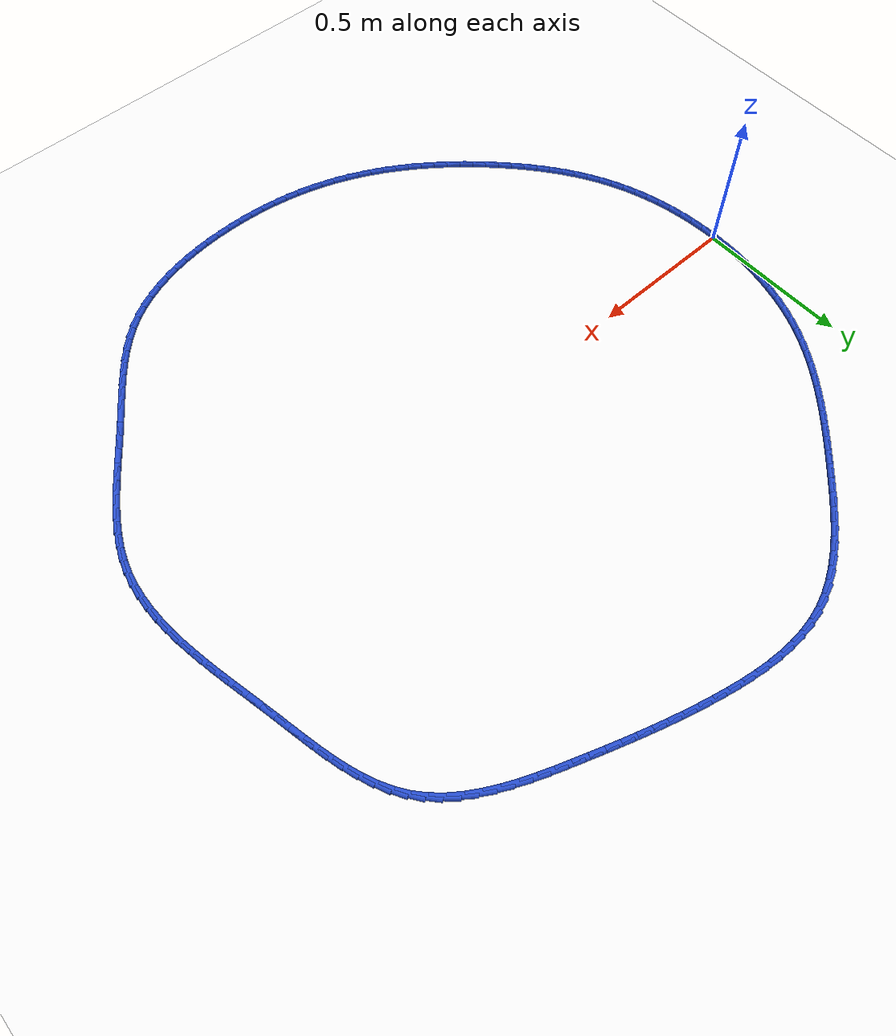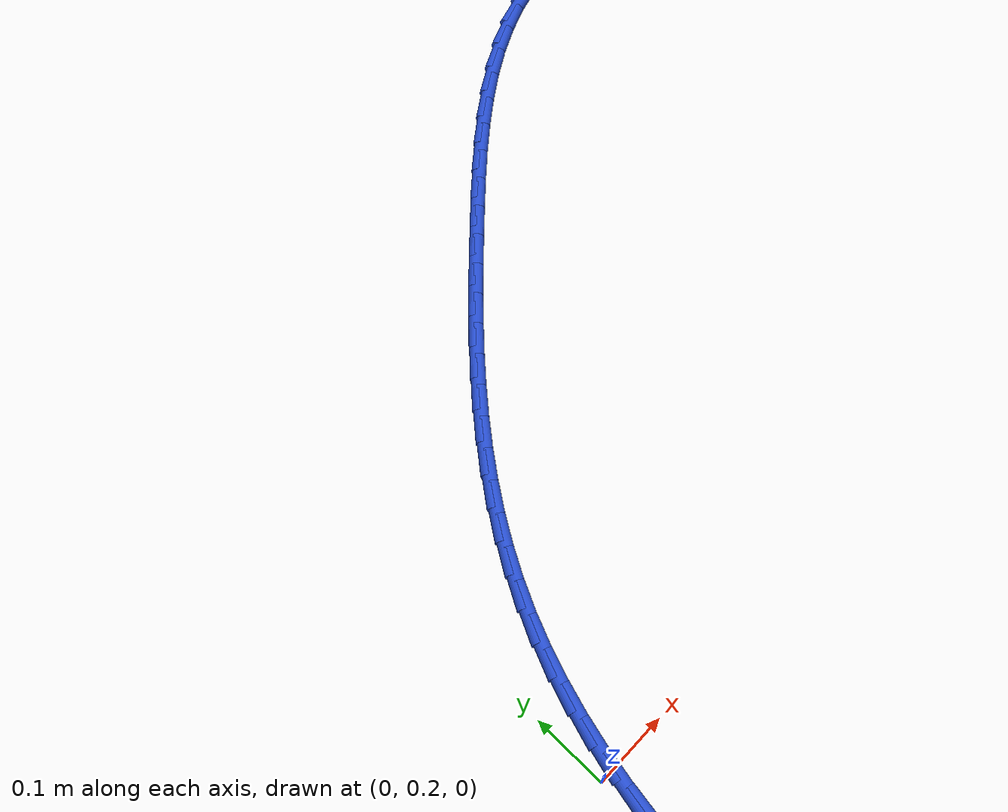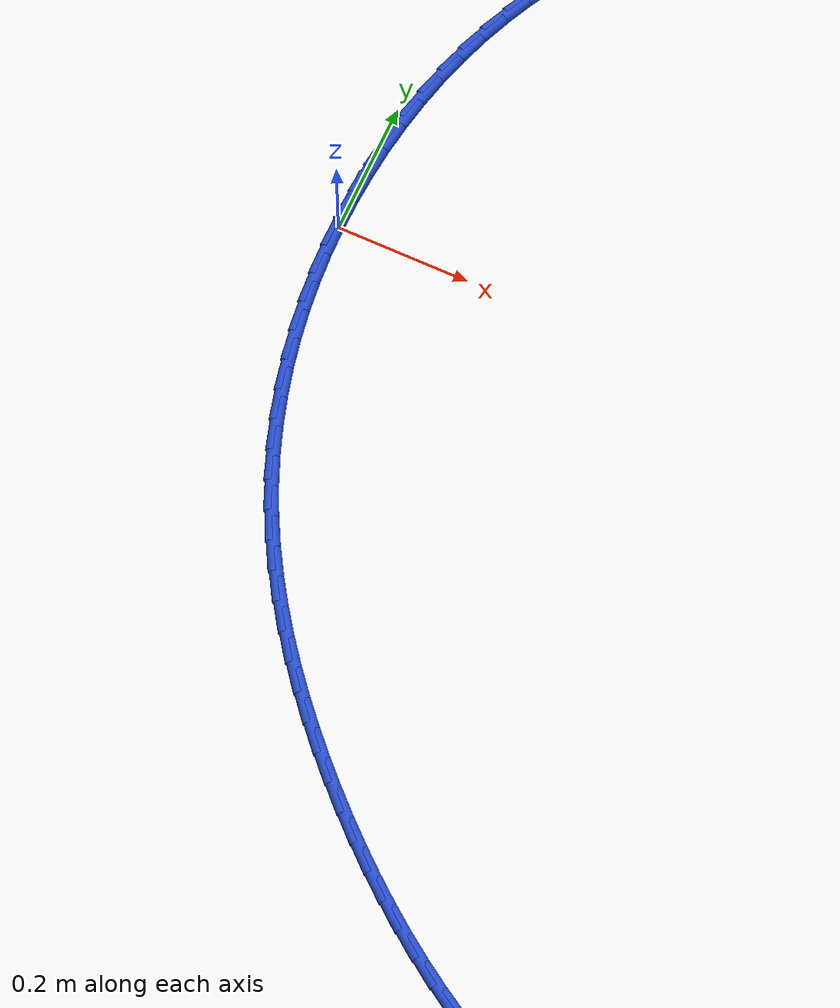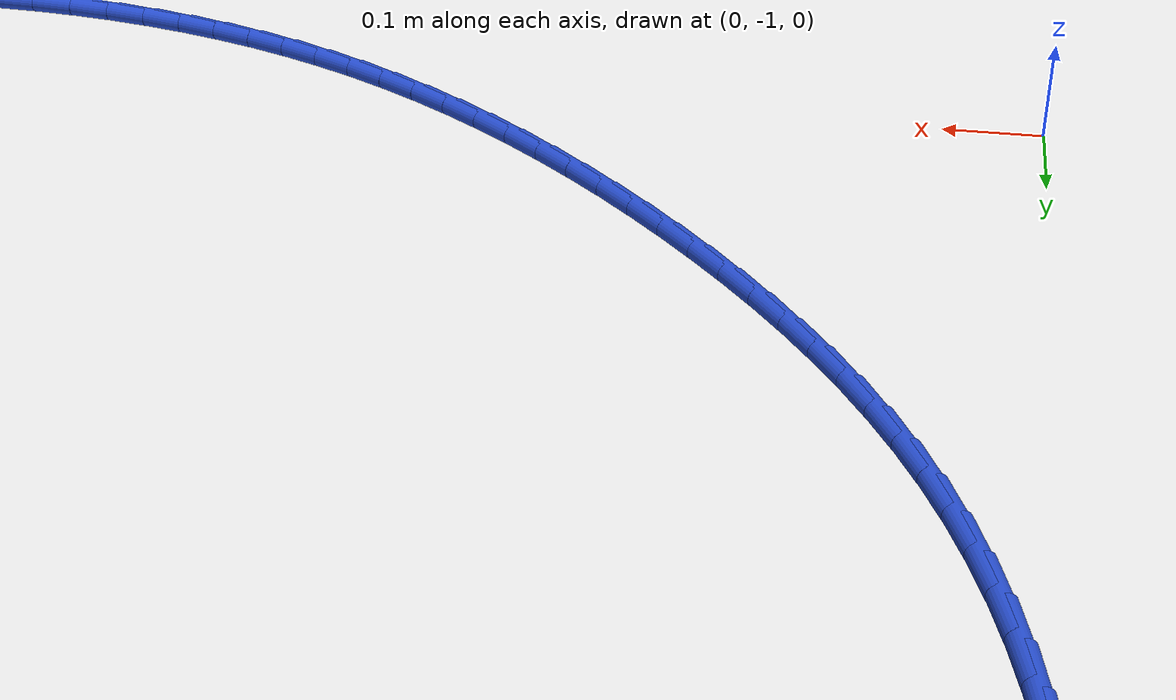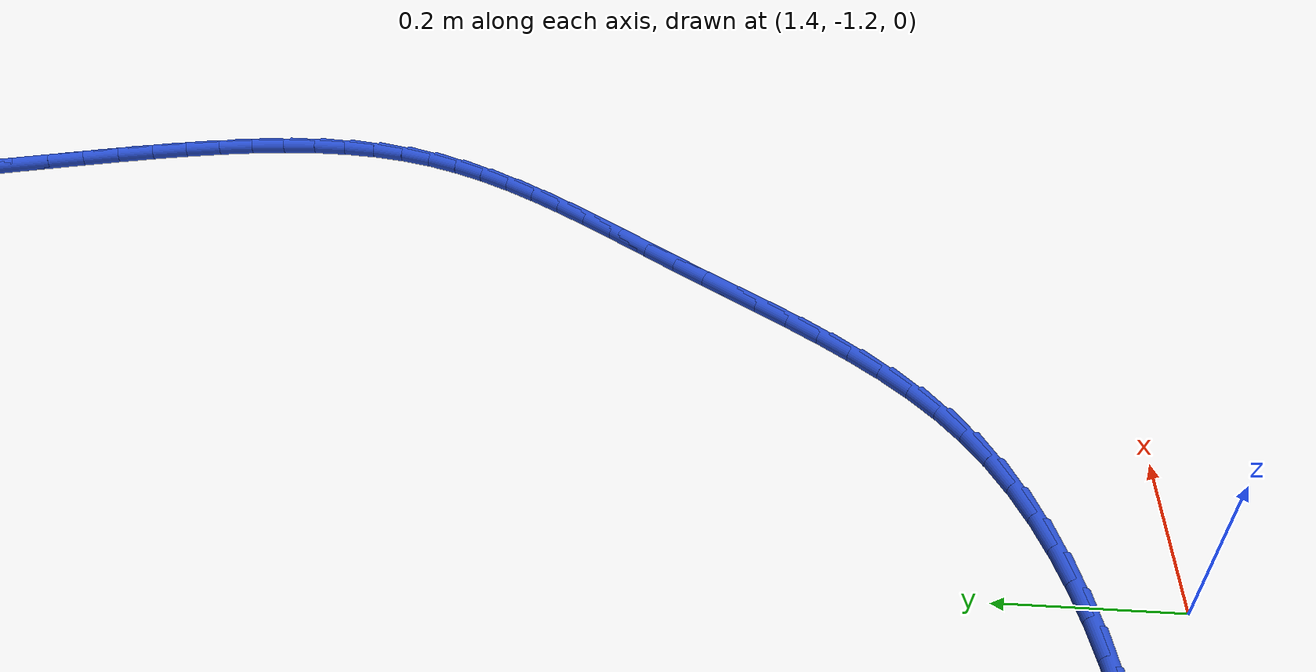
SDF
<sdf version="1.6">
 <world name="default">
  <light name="sun" type="directional">
   <pose>0 0 10 0 -0 0</pose>
   <diffuse>0.8 0.8 0.8 1</diffuse>
   <specular>0.2 0.2 0.2 1</specular>
   <attenuation>
    <range>1000</range>
    <constant>0.9</constant>
    <linear>0.01</linear>
    <quadratic>0.001</quadratic>
   </attenuation>
   <direction>-0.5 0.1 -0.9</direction>
  </light>
  <model name="ground_plane">
   <static>1</static>
   <link name="link">
    <collision name="collision">
     <geometry><plane><normal>0 0 1</normal><size>100 100</size></plane></geometry>
     <surface><friction><ode><mu>100</mu><mu2>50</mu2></ode></friction></surface>
    </collision>
    <visual name="visual">
     <cast_shadows>0</cast_shadows>
     <geometry><plane><normal>0 0 1</normal><size>100 100</size></plane></geometry>
     <material>
      <script><uri>file://media/materials/scripts/gazebo.material</uri><name>Gazebo/WhiteGlow</name></script>
     </material>
    </visual>
   </link>
  </model>
  <gravity>0 0 -9.8</gravity>
  <magnetic_field>6e-06 2.3e-05 -4.2e-05</magnetic_field>
  <atmosphere type="adiabatic"/>
  <physics name="default_physics" default="0" type="ode">
   <max_step_size>0.001</max_step_size>
   <real_time_factor>1</real_time_factor>
   <real_time_update_rate>1000</real_time_update_rate>
  </physics>
  <scene><ambient>0.4 0.4 0.4 1</ambient><background>0.7 0.7 0.7 1</background><shadows>1</shadows></scene>
  <spherical_coordinates>
   <surface_model>EARTH_WGS84</surface_model>
   <latitude_deg>0</latitude_deg>
   <longitude_deg>0</longitude_deg>
   <elevation>0</elevation>
   <heading_deg>0</heading_deg>
  </spherical_coordinates>
  <model name="line">
   <link name="link_0">
    <pose>-3.9898639947466563e-17 1.3877787807814457e-16 0.01 0 1.57 1.5505726882024928</pose>
    <collision name="collision">
     <geometry><cylinder><radius>0.01</radius><length>0.08</length></cylinder></geometry>
    </collision>
    <visual name="visual">
     <material>
      <script><name>Gazebo/Blue</name><uri>file://media/materials/scripts/gazebo.material</uri></script>
     </material>
     <geometry><cylinder><radius>0.01</radius><length>0.08</length></cylinder></geometry>
    </visual>
   </link>
   <link name="link_1">
    <pose>0.0009206554277849331 0.04551752176031066 0.01 0 1.57 1.5070919290253075</pose>
    <collision name="collision">
     <geometry><cylinder><radius>0.01</radius><length>0.08</length></cylinder></geometry>
    </collision>
    <visual name="visual">
     <material>
      <script><name>Gazebo/Blue</name><uri>file://media/materials/scripts/gazebo.material</uri></script>
     </material>
     <geometry><cylinder><radius>0.01</radius><length>0.08</length></cylinder></geometry>
    </visual>
   </link>
   <link name="link_2">
    <pose>0.0038193526490129426 0.09095826130630526 0.01 0 1.57 1.4629954658828586</pose>
    <collision name="collision">
     <geometry><cylinder><radius>0.01</radius><length>0.08</length></cylinder></geometry>
    </collision>
    <visual name="visual">
     <material>
      <script><name>Gazebo/Blue</name><uri>file://media/materials/scripts/gazebo.material</uri></script>
     </material>
     <geometry><cylinder><radius>0.01</radius><length>0.08</length></cylinder></geometry>
    </visual>
   </link>
   <link name="link_3">
    <pose>0.00871308299222229 0.13617829830201303 0.01 0 1.57 1.4180398101255904</pose>
    <collision name="collision">
     <geometry><cylinder><radius>0.01</radius><length>0.08</length></cylinder></geometry>
    </collision>
    <visual name="visual">
     <material>
      <script><name>Gazebo/Blue</name><uri>file://media/materials/scripts/gazebo.material</uri></script>
     </material>
     <geometry><cylinder><radius>0.01</radius><length>0.08</length></cylinder></geometry>
    </visual>
   </link>
   <link name="link_4">
    <pose>0.01561883778595127 0.18103371241146296 0.01 0 1.57 1.3719832310797913</pose>
    <collision name="collision">
     <geometry><cylinder><radius>0.01</radius><length>0.08</length></cylinder></geometry>
    </collision>
    <visual name="visual">
     <material>
      <script><name>Gazebo/Blue</name><uri>file://media/materials/scripts/gazebo.material</uri></script>
     </material>
     <geometry><cylinder><radius>0.01</radius><length>0.08</length></cylinder></geometry>
    </visual>
   </link>
   <link name="link_5">
    <pose>0.024553608358738183 0.22538058329868402 0.01 0 1.57 1.3245864769850098</pose>
    <collision name="collision">
     <geometry><cylinder><radius>0.01</radius><length>0.08</length></cylinder></geometry>
    </collision>
    <visual name="visual">
     <material>
      <script><name>Gazebo/Blue</name><uri>file://media/materials/scripts/gazebo.material</uri></script>
     </material>
     <geometry><cylinder><radius>0.01</radius><length>0.08</length></cylinder></geometry>
    </visual>
   </link>
   <link name="link_6">
    <pose>0.035534386039121325 0.26907499062770524 0.01 0 1.57 1.2756146023325243</pose>
    <collision name="collision">
     <geometry><cylinder><radius>0.01</radius><length>0.08</length></cylinder></geometry>
    </collision>
    <visual name="visual">
     <material>
      <script><name>Gazebo/Blue</name><uri>file://media/materials/scripts/gazebo.material</uri></script>
     </material>
     <geometry><cylinder><radius>0.01</radius><length>0.08</length></cylinder></geometry>
    </visual>
   </link>
   <link name="link_7">
    <pose>0.04857816215563901 0.31197301406255573 0.01 0 1.57 1.2248401965241404</pose>
    <collision name="collision">
     <geometry><cylinder><radius>0.01</radius><length>0.08</length></cylinder></geometry>
    </collision>
    <visual name="visual">
     <material>
      <script><name>Gazebo/Blue</name><uri>file://media/materials/scripts/gazebo.material</uri></script>
     </material>
     <geometry><cylinder><radius>0.01</radius><length>0.08</length></cylinder></geometry>
    </visual>
   </link>
   <link name="link_8">
    <pose>0.06370192803682953 0.35393073326726443 0.01 0 1.57 1.1720483300698943</pose>
    <collision name="collision">
     <geometry><cylinder><radius>0.01</radius><length>0.08</length></cylinder></geometry>
    </collision>
    <visual name="visual">
     <material>
      <script><name>Gazebo/Blue</name><uri>file://media/materials/scripts/gazebo.material</uri></script>
     </material>
     <geometry><cylinder><radius>0.01</radius><length>0.08</length></cylinder></geometry>
    </visual>
   </link>
   <link name="link_9">
    <pose>0.08092267501123115 0.3948042279058602 0.01 0 1.57 1.1173778302438921</pose>
    <collision name="collision">
     <geometry><cylinder><radius>0.01</radius><length>0.08</length></cylinder></geometry>
    </collision>
    <visual name="visual">
     <material>
      <script><name>Gazebo/Blue</name><uri>file://media/materials/scripts/gazebo.material</uri></script>
     </material>
     <geometry><cylinder><radius>0.01</radius><length>0.08</length></cylinder></geometry>
    </visual>
   </link>
   <link name="link_10">
    <pose>0.10024797308178825 0.43446390651374334 0.01 0 1.57 1.0642409342038408</pose>
    <collision name="collision">
     <geometry><cylinder><radius>0.01</radius><length>0.08</length></cylinder></geometry>
    </collision>
    <visual name="visual">
     <material>
      <script><name>Gazebo/Blue</name><uri>file://media/materials/scripts/gazebo.material</uri></script>
     </material>
     <geometry><cylinder><radius>0.01</radius><length>0.08</length></cylinder></geometry>
    </visual>
   </link>
   <link name="link_11">
    <pose>0.12158894984292902 0.472926856652802 0.01 0 1.57 1.014983260659657</pose>
    <collision name="collision">
     <geometry><cylinder><radius>0.01</radius><length>0.08</length></cylinder></geometry>
    </collision>
    <visual name="visual">
     <material>
      <script><name>Gazebo/Blue</name><uri>file://media/materials/scripts/gazebo.material</uri></script>
     </material>
     <geometry><cylinder><radius>0.01</radius><length>0.08</length></cylinder></geometry>
    </visual>
   </link>
   <link name="link_12">
    <pose>0.1448002078739327 0.5102961346441228 0.01 0 1.57 0.9699224637296748</pose>
    <collision name="collision">
     <geometry><cylinder><radius>0.01</radius><length>0.08</length></cylinder></geometry>
    </collision>
    <visual name="visual">
     <material>
      <script><name>Gazebo/Blue</name><uri>file://media/materials/scripts/gazebo.material</uri></script>
     </material>
     <geometry><cylinder><radius>0.01</radius><length>0.08</length></cylinder></geometry>
    </visual>
   </link>
   <link name="link_13">
    <pose>0.16973563342055176 0.5466758862787258 0.01 0 1.57 0.9292327381509493</pose>
    <collision name="collision">
     <geometry><cylinder><radius>0.01</radius><length>0.08</length></cylinder></geometry>
    </collision>
    <visual name="visual">
     <material>
      <script><name>Gazebo/Blue</name><uri>file://media/materials/scripts/gazebo.material</uri></script>
     </material>
     <geometry><cylinder><radius>0.01</radius><length>0.08</length></cylinder></geometry>
    </visual>
   </link>
   <link name="link_14">
    <pose>0.1962491127285387 0.5821702573476304 0.01 0 1.57 0.8929905282355495</pose>
    <collision name="collision">
     <geometry><cylinder><radius>0.01</radius><length>0.08</length></cylinder></geometry>
    </collision>
    <visual name="visual">
     <material>
      <script><name>Gazebo/Blue</name><uri>file://media/materials/scripts/gazebo.material</uri></script>
     </material>
     <geometry><cylinder><radius>0.01</radius><length>0.08</length></cylinder></geometry>
    </visual>
   </link>
   <link name="link_15">
    <pose>0.22419453204364614 0.6168833936418564 0.01 0 1.57 0.8611971430155317</pose>
    <collision name="collision">
     <geometry><cylinder><radius>0.01</radius><length>0.08</length></cylinder></geometry>
    </collision>
    <visual name="visual">
     <material>
      <script><name>Gazebo/Blue</name><uri>file://media/materials/scripts/gazebo.material</uri></script>
     </material>
     <geometry><cylinder><radius>0.01</radius><length>0.08</length></cylinder></geometry>
    </visual>
   </link>
   <link name="link_16">
    <pose>0.25342577761162655 0.6509194409524238 0.01 0 1.57 0.8338007058977134</pose>
    <collision name="collision">
     <geometry><cylinder><radius>0.01</radius><length>0.08</length></cylinder></geometry>
    </collision>
    <visual name="visual">
     <material>
      <script><name>Gazebo/Blue</name><uri>file://media/materials/scripts/gazebo.material</uri></script>
     </material>
     <geometry><cylinder><radius>0.01</radius><length>0.08</length></cylinder></geometry>
    </visual>
   </link>
   <link name="link_17">
    <pose>0.2837967356782323 0.684382545070352 0.01 0 1.57 0.8107156036488731</pose>
    <collision name="collision">
     <geometry><cylinder><radius>0.01</radius><length>0.08</length></cylinder></geometry>
    </collision>
    <visual name="visual">
     <material>
      <script><name>Gazebo/Blue</name><uri>file://media/materials/scripts/gazebo.material</uri></script>
     </material>
     <geometry><cylinder><radius>0.01</radius><length>0.08</length></cylinder></geometry>
    </visual>
   </link>
   <link name="link_18">
    <pose>0.3151612924892162 0.7173768517866611 0.01 0 1.57 0.79183857983386</pose>
    <collision name="collision">
     <geometry><cylinder><radius>0.01</radius><length>0.08</length></cylinder></geometry>
    </collision>
    <visual name="visual">
     <material>
      <script><name>Gazebo/Blue</name><uri>file://media/materials/scripts/gazebo.material</uri></script>
     </material>
     <geometry><cylinder><radius>0.01</radius><length>0.08</length></cylinder></geometry>
    </visual>
   </link>
   <link name="link_19">
    <pose>0.34737333429033057 0.7500065068923707 0.01 0 1.57 0.777061310153667</pose>
    <collision name="collision">
     <geometry><cylinder><radius>0.01</radius><length>0.08</length></cylinder></geometry>
    </collision>
    <visual name="visual">
     <material>
      <script><name>Gazebo/Blue</name><uri>file://media/materials/scripts/gazebo.material</uri></script>
     </material>
     <geometry><cylinder><radius>0.01</radius><length>0.08</length></cylinder></geometry>
    </visual>
   </link>
   <link name="link_20">
    <pose>0.38028674732732776 0.7823756561785002 0.01 0 1.57 0.7662797052062409</pose>
    <collision name="collision">
     <geometry><cylinder><radius>0.01</radius><length>0.08</length></cylinder></geometry>
    </collision>
    <visual name="visual">
     <material>
      <script><name>Gazebo/Blue</name><uri>file://media/materials/scripts/gazebo.material</uri></script>
     </material>
     <geometry><cylinder><radius>0.01</radius><length>0.08</length></cylinder></geometry>
    </visual>
   </link>
   <link name="link_21">
    <pose>0.4137554178459606 0.8145884454360701 0.01 0 1.57 0.7586854684292571</pose>
    <collision name="collision">
     <geometry><cylinder><radius>0.01</radius><length>0.08</length></cylinder></geometry>
    </collision>
    <visual name="visual">
     <material>
      <script><name>Gazebo/Blue</name><uri>file://media/materials/scripts/gazebo.material</uri></script>
     </material>
     <geometry><cylinder><radius>0.01</radius><length>0.08</length></cylinder></geometry>
    </visual>
   </link>
   <link name="link_22">
    <pose>0.44764758871385396 0.8467166154773756 0.01 0 1.57 0.747073268192079</pose>
    <collision name="collision">
     <geometry><cylinder><radius>0.01</radius><length>0.08</length></cylinder></geometry>
    </collision>
    <visual name="visual">
     <material>
      <script><name>Gazebo/Blue</name><uri>file://media/materials/scripts/gazebo.material</uri></script>
     </material>
     <geometry><cylinder><radius>0.01</radius><length>0.08</length></cylinder></geometry>
    </visual>
   </link>
   <link name="link_23">
    <pose>0.48197476527166083 0.8785085429255888 0.01 0 1.57 0.7272052929547193</pose>
    <collision name="collision">
     <geometry><cylinder><radius>0.01</radius><length>0.08</length></cylinder></geometry>
    </collision>
    <visual name="visual">
     <material>
      <script><name>Gazebo/Blue</name><uri>file://media/materials/scripts/gazebo.material</uri></script>
     </material>
     <geometry><cylinder><radius>0.01</radius><length>0.08</length></cylinder></geometry>
    </visual>
   </link>
   <link name="link_24">
    <pose>0.5168307701794242 0.9095268022697054 0.01 0 1.57 0.6986937696179193</pose>
    <collision name="collision">
     <geometry><cylinder><radius>0.01</radius><length>0.08</length></cylinder></geometry>
    </collision>
    <visual name="visual">
     <material>
      <script><name>Gazebo/Blue</name><uri>file://media/materials/scripts/gazebo.material</uri></script>
     </material>
     <geometry><cylinder><radius>0.01</radius><length>0.08</length></cylinder></geometry>
    </visual>
   </link>
   <link name="link_25">
    <pose>0.5523104078257103 0.9393317520949986 0.01 0 1.57 0.6610077217699959</pose>
    <collision name="collision">
     <geometry><cylinder><radius>0.01</radius><length>0.08</length></cylinder></geometry>
    </collision>
    <visual name="visual">
     <material>
      <script><name>Gazebo/Blue</name><uri>file://media/materials/scripts/gazebo.material</uri></script>
     </material>
     <geometry><cylinder><radius>0.01</radius><length>0.08</length></cylinder></geometry>
    </visual>
   </link>
   <link name="link_26">
    <pose>0.5885084825990841 0.9674837509867407 0.01 0 1.57 0.613467626079441</pose>
    <collision name="collision">
     <geometry><cylinder><radius>0.01</radius><length>0.08</length></cylinder></geometry>
    </collision>
    <visual name="visual">
     <material>
      <script><name>Gazebo/Blue</name><uri>file://media/materials/scripts/gazebo.material</uri></script>
     </material>
     <geometry><cylinder><radius>0.01</radius><length>0.08</length></cylinder></geometry>
    </visual>
   </link>
   <link name="link_27">
    <pose>0.6255197988881115 0.9935431575302046 0.01 0 1.57 0.5553227023812817</pose>
    <collision name="collision">
     <geometry><cylinder><radius>0.01</radius><length>0.08</length></cylinder></geometry>
    </collision>
    <visual name="visual">
     <material>
      <script><name>Gazebo/Blue</name><uri>file://media/materials/scripts/gazebo.material</uri></script>
     </material>
     <geometry><cylinder><radius>0.01</radius><length>0.08</length></cylinder></geometry>
    </visual>
   </link>
   <link name="link_28">
    <pose>0.663439161081358 1.0170703303106625 0.01 0 1.57 0.4858836679442088</pose>
    <collision name="collision">
     <geometry><cylinder><radius>0.01</radius><length>0.08</length></cylinder></geometry>
    </collision>
    <visual name="visual">
     <material>
      <script><name>Gazebo/Blue</name><uri>file://media/materials/scripts/gazebo.material</uri></script>
     </material>
     <geometry><cylinder><radius>0.01</radius><length>0.08</length></cylinder></geometry>
    </visual>
   </link>
   <link name="link_29">
    <pose>0.7023613735673893 1.037625627913387 0.01 0 1.57 0.4047315354673868</pose>
    <collision name="collision">
     <geometry><cylinder><radius>0.01</radius><length>0.08</length></cylinder></geometry>
    </collision>
    <visual name="visual">
     <material>
      <script><name>Gazebo/Blue</name><uri>file://media/materials/scripts/gazebo.material</uri></script>
     </material>
     <geometry><cylinder><radius>0.01</radius><length>0.08</length></cylinder></geometry>
    </visual>
   </link>
   <link name="link_30">
    <pose>0.742381240734771 1.0547694089236515 0.01 0 1.57 0.31200529138153793</pose>
    <collision name="collision">
     <geometry><cylinder><radius>0.01</radius><length>0.08</length></cylinder></geometry>
    </collision>
    <visual name="visual">
     <material>
      <script><name>Gazebo/Blue</name><uri>file://media/materials/scripts/gazebo.material</uri></script>
     </material>
     <geometry><cylinder><radius>0.01</radius><length>0.08</length></cylinder></geometry>
    </visual>
   </link>
   <link name="link_31">
    <pose>0.7835935669720688 1.068062031926728 0.01 0 1.57 0.21057127380969712</pose>
    <collision name="collision">
     <geometry><cylinder><radius>0.01</radius><length>0.08</length></cylinder></geometry>
    </collision>
    <visual name="visual">
     <material>
      <script><name>Gazebo/Blue</name><uri>file://media/materials/scripts/gazebo.material</uri></script>
     </material>
     <geometry><cylinder><radius>0.01</radius><length>0.08</length></cylinder></geometry>
    </visual>
   </link>
   <link name="link_32">
    <pose>0.8260629283394837 1.0771394223441038 0.01 0 1.57 0.11527960182350401</pose>
    <collision name="collision">
     <geometry><cylinder><radius>0.01</radius><length>0.08</length></cylinder></geometry>
    </collision>
    <visual name="visual">
     <material>
      <script><name>Gazebo/Blue</name><uri>file://media/materials/scripts/gazebo.material</uri></script>
     </material>
     <geometry><cylinder><radius>0.01</radius><length>0.08</length></cylinder></geometry>
    </visual>
   </link>
   <link name="link_33">
    <pose>0.8696349869689265 1.082184761560779 0.01 0 1.57 0.03234563083166852</pose>
    <collision name="collision">
     <geometry><cylinder><radius>0.01</radius><length>0.08</length></cylinder></geometry>
    </collision>
    <visual name="visual">
     <material>
      <script><name>Gazebo/Blue</name><uri>file://media/materials/scripts/gazebo.material</uri></script>
     </material>
     <geometry><cylinder><radius>0.01</radius><length>0.08</length></cylinder></geometry>
    </visual>
   </link>
   <link name="link_34">
    <pose>0.9140590178168781 1.08362218619458 0.01 0 1.57 -0.03874377640687195</pose>
    <collision name="collision">
     <geometry><cylinder><radius>0.01</radius><length>0.08</length></cylinder></geometry>
    </collision>
    <visual name="visual">
     <material>
      <script><name>Gazebo/Blue</name><uri>file://media/materials/scripts/gazebo.material</uri></script>
     </material>
     <geometry><cylinder><radius>0.01</radius><length>0.08</length></cylinder></geometry>
    </visual>
   </link>
   <link name="link_35">
    <pose>0.9590838770646416 1.0818768797460734 0.01 0 1.57 -0.0989135957534797</pose>
    <collision name="collision">
     <geometry><cylinder><radius>0.01</radius><length>0.08</length></cylinder></geometry>
    </collision>
    <visual name="visual">
     <material>
      <script><name>Gazebo/Blue</name><uri>file://media/materials/scripts/gazebo.material</uri></script>
     </material>
     <geometry><cylinder><radius>0.01</radius><length>0.08</length></cylinder></geometry>
    </visual>
   </link>
   <link name="link_36">
    <pose>1.0044584208935206 1.0773740257158255 0.01 0 1.57 -0.1491965265950681</pose>
    <collision name="collision">
     <geometry><cylinder><radius>0.01</radius><length>0.08</length></cylinder></geometry>
    </collision>
    <visual name="visual">
     <material>
      <script><name>Gazebo/Blue</name><uri>file://media/materials/scripts/gazebo.material</uri></script>
     </material>
     <geometry><cylinder><radius>0.01</radius><length>0.08</length></cylinder></geometry>
    </visual>
   </link>
   <link name="link_37">
    <pose>1.0499315054848184 1.0705388076044042 0.01 0 1.57 -0.19056106430571415</pose>
    <collision name="collision">
     <geometry><cylinder><radius>0.01</radius><length>0.08</length></cylinder></geometry>
    </collision>
    <visual name="visual">
     <material>
      <script><name>Gazebo/Blue</name><uri>file://media/materials/scripts/gazebo.material</uri></script>
     </material>
     <geometry><cylinder><radius>0.01</radius><length>0.08</length></cylinder></geometry>
    </visual>
   </link>
   <link name="link_38">
    <pose>1.0952519870198383 1.0617964089123748 0.01 0 1.57 -0.2238162884499599</pose>
    <collision name="collision">
     <geometry><cylinder><radius>0.01</radius><length>0.08</length></cylinder></geometry>
    </collision>
    <visual name="visual">
     <material>
      <script><name>Gazebo/Blue</name><uri>file://media/materials/scripts/gazebo.material</uri></script>
     </material>
     <geometry><cylinder><radius>0.01</radius><length>0.08</length></cylinder></geometry>
    </visual>
   </link>
   <link name="link_39">
    <pose>1.1401687216798835 1.0515720131403048 0.01 0 1.57 -0.2495638884591143</pose>
    <collision name="collision">
     <geometry><cylinder><radius>0.01</radius><length>0.08</length></cylinder></geometry>
    </collision>
    <visual name="visual">
     <material>
      <script><name>Gazebo/Blue</name><uri>file://media/materials/scripts/gazebo.material</uri></script>
     </material>
     <geometry><cylinder><radius>0.01</radius><length>0.08</length></cylinder></geometry>
    </visual>
   </link>
   <link name="link_40">
    <pose>1.1844307703886015 1.0402906160462495 0.01 0 1.57 -0.2696163956781835</pose>
    <collision name="collision">
     <geometry><cylinder><radius>0.01</radius><length>0.08</length></cylinder></geometry>
    </collision>
    <visual name="visual">
     <material>
      <script><name>Gazebo/Blue</name><uri>file://media/materials/scripts/gazebo.material</uri></script>
     </material>
     <geometry><cylinder><radius>0.01</radius><length>0.08</length></cylinder></geometry>
    </visual>
   </link>
   <link name="link_41">
    <pose>1.2278932415698285 1.0282799710518098 0.01 0 1.57 -0.28778578197098575</pose>
    <collision name="collision">
     <geometry><cylinder><radius>0.01</radius><length>0.08</length></cylinder></geometry>
    </collision>
    <visual name="visual">
     <material>
      <script><name>Gazebo/Blue</name><uri>file://media/materials/scripts/gazebo.material</uri></script>
     </material>
     <geometry><cylinder><radius>0.01</radius><length>0.08</length></cylinder></geometry>
    </visual>
   </link>
   <link name="link_42">
    <pose>1.2706903502010494 1.0156118993468124 0.01 0 1.57 -0.3044557159259365</pose>
    <collision name="collision">
     <geometry><cylinder><radius>0.01</radius><length>0.08</length></cylinder></geometry>
    </collision>
    <visual name="visual">
     <material>
      <script><name>Gazebo/Blue</name><uri>file://media/materials/scripts/gazebo.material</uri></script>
     </material>
     <geometry><cylinder><radius>0.01</radius><length>0.08</length></cylinder></geometry>
    </visual>
   </link>
   <link name="link_43">
    <pose>1.313001684657963 1.0023166160931496 0.01 0 1.57 -0.31940394249271786</pose>
    <collision name="collision">
     <geometry><cylinder><radius>0.01</radius><length>0.08</length></cylinder></geometry>
    </collision>
    <visual name="visual">
     <material>
      <script><name>Gazebo/Blue</name><uri>file://media/materials/scripts/gazebo.material</uri></script>
     </material>
     <geometry><cylinder><radius>0.01</radius><length>0.08</length></cylinder></geometry>
    </visual>
   </link>
   <link name="link_44">
    <pose>1.3550068333162675 0.9884243364527155 0.01 0 1.57 -0.33244741905310193</pose>
    <collision name="collision">
     <geometry><cylinder><radius>0.01</radius><length>0.08</length></cylinder></geometry>
    </collision>
    <visual name="visual">
     <material>
      <script><name>Gazebo/Blue</name><uri>file://media/materials/scripts/gazebo.material</uri></script>
     </material>
     <geometry><cylinder><radius>0.01</radius><length>0.08</length></cylinder></geometry>
    </visual>
   </link>
   <link name="link_45">
    <pose>1.3968853845516613 0.9739652755874015 0.01 0 1.57 -0.3434484988253575</pose>
    <collision name="collision">
     <geometry><cylinder><radius>0.01</radius><length>0.08</length></cylinder></geometry>
    </collision>
    <visual name="visual">
     <material>
      <script><name>Gazebo/Blue</name><uri>file://media/materials/scripts/gazebo.material</uri></script>
     </material>
     <geometry><cylinder><radius>0.01</radius><length>0.08</length></cylinder></geometry>
    </visual>
   </link>
   <link name="link_46">
    <pose>1.438816926739843 0.958969648659101 0.01 0 1.57 -0.3523183889713917</pose>
    <collision name="collision">
     <geometry><cylinder><radius>0.01</radius><length>0.08</length></cylinder></geometry>
    </collision>
    <visual name="visual">
     <material>
      <script><name>Gazebo/Blue</name><uri>file://media/materials/scripts/gazebo.material</uri></script>
     </material>
     <geometry><cylinder><radius>0.01</radius><length>0.08</length></cylinder></geometry>
    </visual>
   </link>
   <link name="link_47">
    <pose>1.4809810482565113 0.9434676708297068 0.01 0 1.57 -0.35901785134265835</pose>
    <collision name="collision">
     <geometry><cylinder><radius>0.01</radius><length>0.08</length></cylinder></geometry>
    </collision>
    <visual name="visual">
     <material>
      <script><name>Gazebo/Blue</name><uri>file://media/materials/scripts/gazebo.material</uri></script>
     </material>
     <geometry><cylinder><radius>0.01</radius><length>0.08</length></cylinder></geometry>
    </visual>
   </link>
   <link name="link_48">
    <pose>1.523557337477364 0.9274895572611118 0.01 0 1.57 -0.3642870130882982</pose>
    <collision name="collision">
     <geometry><cylinder><radius>0.01</radius><length>0.08</length></cylinder></geometry>
    </collision>
    <visual name="visual">
     <material>
      <script><name>Gazebo/Blue</name><uri>file://media/materials/scripts/gazebo.material</uri></script>
     </material>
     <geometry><cylinder><radius>0.01</radius><length>0.08</length></cylinder></geometry>
    </visual>
   </link>
   <link name="link_49">
    <pose>1.566681952457323 0.9110459179435783 0.01 0 1.57 -0.37493434596219144</pose>
    <collision name="collision">
     <geometry><cylinder><radius>0.01</radius><length>0.08</length></cylinder></geometry>
    </collision>
    <visual name="visual">
     <material>
      <script><name>Gazebo/Blue</name><uri>file://media/materials/scripts/gazebo.material</uri></script>
     </material>
     <geometry><cylinder><radius>0.01</radius><length>0.08</length></cylinder></geometry>
    </visual>
   </link>
   <link name="link_50">
    <pose>1.6100856525923446 0.8939643591467991 0.01 0 1.57 -0.394686479308191</pose>
    <collision name="collision">
     <geometry><cylinder><radius>0.01</radius><length>0.08</length></cylinder></geometry>
    </collision>
    <visual name="visual">
     <material>
      <script><name>Gazebo/Blue</name><uri>file://media/materials/scripts/gazebo.material</uri></script>
     </material>
     <geometry><cylinder><radius>0.01</radius><length>0.08</length></cylinder></geometry>
    </visual>
   </link>
   <link name="link_51">
    <pose>1.6532782498113927 0.8759727477663592 0.01 0 1.57 -0.42392427258061693</pose>
    <collision name="collision">
     <geometry><cylinder><radius>0.01</radius><length>0.08</length></cylinder></geometry>
    </collision>
    <visual name="visual">
     <material>
      <script><name>Gazebo/Blue</name><uri>file://media/materials/scripts/gazebo.material</uri></script>
     </material>
     <geometry><cylinder><radius>0.01</radius><length>0.08</length></cylinder></geometry>
    </visual>
   </link>
   <link name="link_52">
    <pose>1.695767332375506 0.8567979468970287 0.01 0 1.57 -0.46334822507391676</pose>
    <collision name="collision">
     <geometry><cylinder><radius>0.01</radius><length>0.08</length></cylinder></geometry>
    </collision>
    <visual name="visual">
     <material>
      <script><name>Gazebo/Blue</name><uri>file://media/materials/scripts/gazebo.material</uri></script>
     </material>
     <geometry><cylinder><radius>0.01</radius><length>0.08</length></cylinder></geometry>
    </visual>
   </link>
   <link name="link_53">
    <pose>1.7370604885457226 0.8361668196335781 0.01 0 1.57 -0.5139777343200697</pose>
    <collision name="collision">
     <geometry><cylinder><radius>0.01</radius><length>0.08</length></cylinder></geometry>
    </collision>
    <visual name="visual">
     <material>
      <script><name>Gazebo/Blue</name><uri>file://media/materials/scripts/gazebo.material</uri></script>
     </material>
     <geometry><cylinder><radius>0.01</radius><length>0.08</length></cylinder></geometry>
    </visual>
   </link>
   <link name="link_54">
    <pose>1.776665306583079 0.8138062290707766 0.01 0 1.57 -0.57708018404111</pose>
    <collision name="collision">
     <geometry><cylinder><radius>0.01</radius><length>0.08</length></cylinder></geometry>
    </collision>
    <visual name="visual">
     <material>
      <script><name>Gazebo/Blue</name><uri>file://media/materials/scripts/gazebo.material</uri></script>
     </material>
     <geometry><cylinder><radius>0.01</radius><length>0.08</length></cylinder></geometry>
    </visual>
   </link>
   <link name="link_55">
    <pose>1.8140893747486138 0.7894430383033955 0.01 0 1.57 -0.6540204884061762</pose>
    <collision name="collision">
     <geometry><cylinder><radius>0.01</radius><length>0.08</length></cylinder></geometry>
    </collision>
    <visual name="visual">
     <material>
      <script><name>Gazebo/Blue</name><uri>file://media/materials/scripts/gazebo.material</uri></script>
     </material>
     <geometry><cylinder><radius>0.01</radius><length>0.08</length></cylinder></geometry>
    </visual>
   </link>
   <link name="link_56">
    <pose>1.8488402813033646 0.7628041104262046 0.01 0 1.57 -0.7459680981970288</pose>
    <collision name="collision">
     <geometry><cylinder><radius>0.01</radius><length>0.08</length></cylinder></geometry>
    </collision>
    <visual name="visual">
     <material>
      <script><name>Gazebo/Blue</name><uri>file://media/materials/scripts/gazebo.material</uri></script>
     </material>
     <geometry><cylinder><radius>0.01</radius><length>0.08</length></cylinder></geometry>
    </visual>
   </link>
   <link name="link_57">
    <pose>1.8804256145083689 0.7336163085339739 0.01 0 1.57 -0.8533517528467636</pose>
    <collision name="collision">
     <geometry><cylinder><radius>0.01</radius><length>0.08</length></cylinder></geometry>
    </collision>
    <visual name="visual">
     <material>
      <script><name>Gazebo/Blue</name><uri>file://media/materials/scripts/gazebo.material</uri></script>
     </material>
     <geometry><cylinder><radius>0.01</radius><length>0.08</length></cylinder></geometry>
    </visual>
   </link>
   <link name="link_58">
    <pose>1.908354931866206 0.7016077140418595 0.01 0 1.57 -0.9670909521451104</pose>
    <collision name="collision">
     <geometry><cylinder><radius>0.01</radius><length>0.08</length></cylinder></geometry>
    </collision>
    <visual name="visual">
     <material>
      <script><name>Gazebo/Blue</name><uri>file://media/materials/scripts/gazebo.material</uri></script>
     </material>
     <geometry><cylinder><radius>0.01</radius><length>0.08</length></cylinder></geometry>
    </visual>
   </link>
   <link name="link_59">
    <pose>1.9324340558594766 0.666689700082842 0.01 0 1.57 -1.0679960847927985</pose>
    <collision name="collision">
     <geometry><cylinder><radius>0.01</radius><length>0.08</length></cylinder></geometry>
    </collision>
    <visual name="visual">
     <material>
      <script><name>Gazebo/Blue</name><uri>file://media/materials/scripts/gazebo.material</uri></script>
     </material>
     <geometry><cylinder><radius>0.01</radius><length>0.08</length></cylinder></geometry>
    </visual>
   </link>
   <link name="link_60">
    <pose>1.9530783715334596 0.6291507608699078 0.01 0 1.57 -1.1525725775517304</pose>
    <collision name="collision">
     <geometry><cylinder><radius>0.01</radius><length>0.08</length></cylinder></geometry>
    </collision>
    <visual name="visual">
     <material>
      <script><name>Gazebo/Blue</name><uri>file://media/materials/scripts/gazebo.material</uri></script>
     </material>
     <geometry><cylinder><radius>0.01</radius><length>0.08</length></cylinder></geometry>
    </visual>
   </link>
   <link name="link_61">
    <pose>1.970778316034172 0.5893258234697322 0.01 0 1.57 -1.2208686324024014</pose>
    <collision name="collision">
     <geometry><cylinder><radius>0.01</radius><length>0.08</length></cylinder></geometry>
    </collision>
    <visual name="visual">
     <material>
      <script><name>Gazebo/Blue</name><uri>file://media/materials/scripts/gazebo.material</uri></script>
     </material>
     <geometry><cylinder><radius>0.01</radius><length>0.08</length></cylinder></geometry>
    </visual>
   </link>
   <link name="link_62">
    <pose>1.9860243265076305 0.54754981494899 0.01 0 1.57 -1.2737489380996596</pose>
    <collision name="collision">
     <geometry><cylinder><radius>0.01</radius><length>0.08</length></cylinder></geometry>
    </collision>
    <visual name="visual">
     <material>
      <script><name>Gazebo/Blue</name><uri>file://media/materials/scripts/gazebo.material</uri></script>
     </material>
     <geometry><cylinder><radius>0.01</radius><length>0.08</length></cylinder></geometry>
    </visual>
   </link>
   <link name="link_63">
    <pose>1.9993068400998517 0.5041576623743579 0.01 0 1.57 -1.3123570258026274</pose>
    <collision name="collision">
     <geometry><cylinder><radius>0.01</radius><length>0.08</length></cylinder></geometry>
    </collision>
    <visual name="visual">
     <material>
      <script><name>Gazebo/Blue</name><uri>file://media/materials/scripts/gazebo.material</uri></script>
     </material>
     <geometry><cylinder><radius>0.01</radius><length>0.08</length></cylinder></geometry>
    </visual>
   </link>
   <link name="link_64">
    <pose>2.011116293956853 0.45948429281251096 0.01 0 1.57 -1.3377791675958628</pose>
    <collision name="collision">
     <geometry><cylinder><radius>0.01</radius><length>0.08</length></cylinder></geometry>
    </collision>
    <visual name="visual">
     <material>
      <script><name>Gazebo/Blue</name><uri>file://media/materials/scripts/gazebo.material</uri></script>
     </material>
     <geometry><cylinder><radius>0.01</radius><length>0.08</length></cylinder></geometry>
    </visual>
   </link>
   <link name="link_65">
    <pose>2.021943125224651 0.4138646333301245 0.01 0 1.57 -1.3508686073525271</pose>
    <collision name="collision">
     <geometry><cylinder><radius>0.01</radius><length>0.08</length></cylinder></geometry>
    </collision>
    <visual name="visual">
     <material>
      <script><name>Gazebo/Blue</name><uri>file://media/materials/scripts/gazebo.material</uri></script>
     </material>
     <geometry><cylinder><radius>0.01</radius><length>0.08</length></cylinder></geometry>
    </visual>
   </link>
   <link name="link_66">
    <pose>2.0322777710492623 0.3676336109938739 0.01 0 1.57 -1.3521702704656968</pose>
    <collision name="collision">
     <geometry><cylinder><radius>0.01</radius><length>0.08</length></cylinder></geometry>
    </collision>
    <visual name="visual">
     <material>
      <script><name>Gazebo/Blue</name><uri>file://media/materials/scripts/gazebo.material</uri></script>
     </material>
     <geometry><cylinder><radius>0.01</radius><length>0.08</length></cylinder></geometry>
    </visual>
   </link>
   <link name="link_67">
    <pose>2.0426106685767036 0.3211261528704345 0.01 0 1.57 -1.344513946417605</pose>
    <collision name="collision">
     <geometry><cylinder><radius>0.01</radius><length>0.08</length></cylinder></geometry>
    </collision>
    <visual name="visual">
     <material>
      <script><name>Gazebo/Blue</name><uri>file://media/materials/scripts/gazebo.material</uri></script>
     </material>
     <geometry><cylinder><radius>0.01</radius><length>0.08</length></cylinder></geometry>
    </visual>
   </link>
   <link name="link_68">
    <pose>2.0533141317297177 0.2746349025500666 0.01 0 1.57 -1.3395813190860317</pose>
    <collision name="collision">
     <geometry><cylinder><radius>0.01</radius><length>0.08</length></cylinder></geometry>
    </collision>
    <visual name="visual">
     <material>
      <script><name>Gazebo/Blue</name><uri>file://media/materials/scripts/gazebo.material</uri></script>
     </material>
     <geometry><cylinder><radius>0.01</radius><length>0.08</length></cylinder></geometry>
    </visual>
   </link>
   <link name="link_69">
    <pose>2.0642312392265945 0.22826305819760448 0.01 0 1.57 -1.3406379872564995</pose>
    <collision name="collision">
     <geometry><cylinder><radius>0.01</radius><length>0.08</length></cylinder></geometry>
    </collision>
    <visual name="visual">
     <material>
      <script><name>Gazebo/Blue</name><uri>file://media/materials/scripts/gazebo.material</uri></script>
     </material>
     <geometry><cylinder><radius>0.01</radius><length>0.08</length></cylinder></geometry>
    </visual>
   </link>
   <link name="link_70">
    <pose>2.0750569122004707 0.18206078337906312 0.01 0 1.57 -1.3477628396357368</pose>
    <collision name="collision">
     <geometry><cylinder><radius>0.01</radius><length>0.08</length></cylinder></geometry>
    </collision>
    <visual name="visual">
     <material>
      <script><name>Gazebo/Blue</name><uri>file://media/materials/scripts/gazebo.material</uri></script>
     </material>
     <geometry><cylinder><radius>0.01</radius><length>0.08</length></cylinder></geometry>
    </visual>
   </link>
   <link name="link_71">
    <pose>2.0854860646392206 0.13607823910273373 0.01 0 1.57 -1.361126144048252</pose>
    <collision name="collision">
     <geometry><cylinder><radius>0.01</radius><length>0.08</length></cylinder></geometry>
    </collision>
    <visual name="visual">
     <material>
      <script><name>Gazebo/Blue</name><uri>file://media/materials/scripts/gazebo.material</uri></script>
     </material>
     <geometry><cylinder><radius>0.01</radius><length>0.08</length></cylinder></geometry>
    </visual>
   </link>
   <link name="link_72">
    <pose>2.095213610530719 0.09036558637690878 0.01 0 1.57 -1.3809884703647464</pose>
    <collision name="collision">
     <geometry><cylinder><radius>0.01</radius><length>0.08</length></cylinder></geometry>
    </collision>
    <visual name="visual">
     <material>
      <script><name>Gazebo/Blue</name><uri>file://media/materials/scripts/gazebo.material</uri></script>
     </material>
     <geometry><cylinder><radius>0.01</radius><length>0.08</length></cylinder></geometry>
    </visual>
   </link>
   <link name="link_73">
    <pose>2.10393446386284 0.04497298620987952 0.01 0 1.57 -1.4076939500851235</pose>
    <collision name="collision">
     <geometry><cylinder><radius>0.01</radius><length>0.08</length></cylinder></geometry>
    </collision>
    <visual name="visual">
     <material>
      <script><name>Gazebo/Blue</name><uri>file://media/materials/scripts/gazebo.material</uri></script>
     </material>
     <geometry><cylinder><radius>0.01</radius><length>0.08</length></cylinder></geometry>
    </visual>
   </link>
   <link name="link_74">
    <pose>2.1113435386234594 -4.940039006224098e-05 0.01 0 1.57 -1.441654745440006</pose>
    <collision name="collision">
     <geometry><cylinder><radius>0.01</radius><length>0.08</length></cylinder></geometry>
    </collision>
    <visual name="visual">
     <material>
      <script><name>Gazebo/Blue</name><uri>file://media/materials/scripts/gazebo.material</uri></script>
     </material>
     <geometry><cylinder><radius>0.01</radius><length>0.08</length></cylinder></geometry>
    </visual>
   </link>
   <link name="link_75">
    <pose>2.117135748800451 -0.044651412414624905 0.01 0 1.57 -1.483321731270571</pose>
    <collision name="collision">
     <geometry><cylinder><radius>0.01</radius><length>0.08</length></cylinder></geometry>
    </collision>
    <visual name="visual">
     <material>
      <script><name>Gazebo/Blue</name><uri>file://media/materials/scripts/gazebo.material</uri></script>
     </material>
     <geometry><cylinder><radius>0.01</radius><length>0.08</length></cylinder></geometry>
    </visual>
   </link>
   <link name="link_76">
    <pose>2.1210060083816904 -0.08878288885551706 0.01 0 1.57 -1.5331348587512796</pose>
    <collision name="collision">
     <geometry><cylinder><radius>0.01</radius><length>0.08</length></cylinder></geometry>
    </collision>
    <visual name="visual">
     <material>
      <script><name>Gazebo/Blue</name><uri>file://media/materials/scripts/gazebo.material</uri></script>
     </material>
     <geometry><cylinder><radius>0.01</radius><length>0.08</length></cylinder></geometry>
    </visual>
   </link>
   <link name="link_77">
    <pose>2.122649231355051 -0.1323936687044467 0.01 0 1.57 1.5501463523527739</pose>
    <collision name="collision">
     <geometry><cylinder><radius>0.01</radius><length>0.08</length></cylinder></geometry>
    </collision>
    <visual name="visual">
     <material>
      <script><name>Gazebo/Blue</name><uri>file://media/materials/scripts/gazebo.material</uri></script>
     </material>
     <geometry><cylinder><radius>0.01</radius><length>0.08</length></cylinder></geometry>
    </visual>
   </link>
   <link name="link_78">
    <pose>2.1217603317084093 -0.1754335909531214 0.01 0 1.57 1.483180463637573</pose>
    <collision name="collision">
     <geometry><cylinder><radius>0.01</radius><length>0.08</length></cylinder></geometry>
    </collision>
    <visual name="visual">
     <material>
      <script><name>Gazebo/Blue</name><uri>file://media/materials/scripts/gazebo.material</uri></script>
     </material>
     <geometry><cylinder><radius>0.01</radius><length>0.08</length></cylinder></geometry>
    </visual>
   </link>
   <link name="link_79">
    <pose>2.1180342234296385 -0.21785249459325084 0.01 0 1.57 1.4077354511814084</pose>
    <collision name="collision">
     <geometry><cylinder><radius>0.01</radius><length>0.08</length></cylinder></geometry>
    </collision>
    <visual name="visual">
     <material>
      <script><name>Gazebo/Blue</name><uri>file://media/materials/scripts/gazebo.material</uri></script>
     </material>
     <geometry><cylinder><radius>0.01</radius><length>0.08</length></cylinder></geometry>
    </visual>
   </link>
   <link name="link_80">
    <pose>2.1111658205066135 -0.2596002186165419 0.01 0 1.57 1.3245697374175465</pose>
    <collision name="collision">
     <geometry><cylinder><radius>0.01</radius><length>0.08</length></cylinder></geometry>
    </collision>
    <visual name="visual">
     <material>
      <script><name>Gazebo/Blue</name><uri>file://media/materials/scripts/gazebo.material</uri></script>
     </material>
     <geometry><cylinder><radius>0.01</radius><length>0.08</length></cylinder></geometry>
    </visual>
   </link>
   <link name="link_81">
    <pose>2.1008545687960254 -0.3006275612726654 0.01 0 1.57 1.2413383697773763</pose>
    <collision name="collision">
     <geometry><cylinder><radius>0.01</radius><length>0.08</length></cylinder></geometry>
    </collision>
    <visual name="visual">
     <material>
      <script><name>Gazebo/Blue</name><uri>file://media/materials/scripts/gazebo.material</uri></script>
     </material>
     <geometry><cylinder><radius>0.01</radius><length>0.08</length></cylinder></geometry>
    </visual>
   </link>
   <link name="link_82">
    <pose>2.087070107203448 -0.34094251241229756 0.01 0 1.57 1.168965172644767</pose>
    <collision name="collision">
     <geometry><cylinder><radius>0.01</radius><length>0.08</length></cylinder></geometry>
    </collision>
    <visual name="visual">
     <material>
      <script><name>Gazebo/Blue</name><uri>file://media/materials/scripts/gazebo.material</uri></script>
     </material>
     <geometry><cylinder><radius>0.01</radius><length>0.08</length></cylinder></geometry>
    </visual>
   </link>
   <link name="link_83">
    <pose>2.070199888368588 -0.3806415002692515 0.01 0 1.57 1.1083911365597328</pose>
    <collision name="collision">
     <geometry><cylinder><radius>0.01</radius><length>0.08</length></cylinder></geometry>
    </collision>
    <visual name="visual">
     <material>
      <script><name>Gazebo/Blue</name><uri>file://media/materials/scripts/gazebo.material</uri></script>
     </material>
     <geometry><cylinder><radius>0.01</radius><length>0.08</length></cylinder></geometry>
    </visual>
   </link>
   <link name="link_84">
    <pose>2.0506671909624328 -0.41982853635195 0.01 0 1.57 1.0592171250427465</pose>
    <collision name="collision">
     <geometry><cylinder><radius>0.01</radius><length>0.08</length></cylinder></geometry>
    </collision>
    <visual name="visual">
     <material>
      <script><name>Gazebo/Blue</name><uri>file://media/materials/scripts/gazebo.material</uri></script>
     </material>
     <geometry><cylinder><radius>0.01</radius><length>0.08</length></cylinder></geometry>
    </visual>
   </link>
   <link name="link_85">
    <pose>2.0288952936559723 -0.4586076321688136 0.01 0 1.57 1.0208247940489334</pose>
    <collision name="collision">
     <geometry><cylinder><radius>0.01</radius><length>0.08</length></cylinder></geometry>
    </collision>
    <visual name="visual">
     <material>
      <script><name>Gazebo/Blue</name><uri>file://media/materials/scripts/gazebo.material</uri></script>
     </material>
     <geometry><cylinder><radius>0.01</radius><length>0.08</length></cylinder></geometry>
    </visual>
   </link>
   <link name="link_86">
    <pose>2.0053074751201936 -0.4970827992282649 0.01 0 1.57 0.9925582580937964</pose>
    <collision name="collision">
     <geometry><cylinder><radius>0.01</radius><length>0.08</length></cylinder></geometry>
    </collision>
    <visual name="visual">
     <material>
      <script><name>Gazebo/Blue</name><uri>file://media/materials/scripts/gazebo.material</uri></script>
     </material>
     <geometry><cylinder><radius>0.01</radius><length>0.08</length></cylinder></geometry>
    </visual>
   </link>
   <link name="link_87">
    <pose>1.9803270140260865 -0.5353580490387251 0.01 0 1.57 0.9738369358224979</pose>
    <collision name="collision">
     <geometry><cylinder><radius>0.01</radius><length>0.08</length></cylinder></geometry>
    </collision>
    <visual name="visual">
     <material>
      <script><name>Gazebo/Blue</name><uri>file://media/materials/scripts/gazebo.material</uri></script>
     </material>
     <geometry><cylinder><radius>0.01</radius><length>0.08</length></cylinder></geometry>
    </visual>
   </link>
   <link name="link_88">
    <pose>1.9543771890446393 -0.573537393108615 0.01 0 1.57 0.9642178031817733</pose>
    <collision name="collision">
     <geometry><cylinder><radius>0.01</radius><length>0.08</length></cylinder></geometry>
    </collision>
    <visual name="visual">
     <material>
      <script><name>Gazebo/Blue</name><uri>file://media/materials/scripts/gazebo.material</uri></script>
     </material>
     <geometry><cylinder><radius>0.01</radius><length>0.08</length></cylinder></geometry>
    </visual>
   </link>
   <link name="link_89">
    <pose>1.92788127884684 -0.6117248429463574 0.01 0 1.57 0.9634248427808662</pose>
    <collision name="collision">
     <geometry><cylinder><radius>0.01</radius><length>0.08</length></cylinder></geometry>
    </collision>
    <visual name="visual">
     <material>
      <script><name>Gazebo/Blue</name><uri>file://media/materials/scripts/gazebo.material</uri></script>
     </material>
     <geometry><cylinder><radius>0.01</radius><length>0.08</length></cylinder></geometry>
    </visual>
   </link>
   <link name="link_90">
    <pose>1.9012625621036778 -0.6500244100603734 0.01 0 1.57 0.9713073079931377</pose>
    <collision name="collision">
     <geometry><cylinder><radius>0.01</radius><length>0.08</length></cylinder></geometry>
    </collision>
    <visual name="visual">
     <material>
      <script><name>Gazebo/Blue</name><uri>file://media/materials/scripts/gazebo.material</uri></script>
     </material>
     <geometry><cylinder><radius>0.01</radius><length>0.08</length></cylinder></geometry>
    </visual>
   </link>
   <link name="link_91">
    <pose>1.8749422973057186 -0.6885388500080164 0.01 0 1.57 0.9817716032266591</pose>
    <collision name="collision">
     <geometry><cylinder><radius>0.01</radius><length>0.08</length></cylinder></geometry>
    </collision>
    <visual name="visual">
     <material>
      <script><name>Gazebo/Blue</name><uri>file://media/materials/scripts/gazebo.material</uri></script>
     </material>
     <geometry><cylinder><radius>0.01</radius><length>0.08</length></cylinder></geometry>
    </visual>
   </link>
   <link name="link_92">
    <pose>1.8490980909558532 -0.7272194393151213 0.01 0 1.57 0.9829027595713841</pose>
    <collision name="collision">
     <geometry><cylinder><radius>0.01</radius><length>0.08</length></cylinder></geometry>
    </collision>
    <visual name="visual">
     <material>
      <script><name>Gazebo/Blue</name><uri>file://media/materials/scripts/gazebo.material</uri></script>
     </material>
     <geometry><cylinder><radius>0.01</radius><length>0.08</length></cylinder></geometry>
    </visual>
   </link>
   <link name="link_93">
    <pose>1.8234347653757477 -0.7657235234356904 0.01 0 1.57 0.9731680264339136</pose>
    <collision name="collision">
     <geometry><cylinder><radius>0.01</radius><length>0.08</length></cylinder></geometry>
    </collision>
    <visual name="visual">
     <material>
      <script><name>Gazebo/Blue</name><uri>file://media/materials/scripts/gazebo.material</uri></script>
     </material>
     <geometry><cylinder><radius>0.01</radius><length>0.08</length></cylinder></geometry>
    </visual>
   </link>
   <link name="link_94">
    <pose>1.7976028821614398 -0.8036747137990409 0.01 0 1.57 0.9522362246229236</pose>
    <collision name="collision">
     <geometry><cylinder><radius>0.01</radius><length>0.08</length></cylinder></geometry>
    </collision>
    <visual name="visual">
     <material>
      <script><name>Gazebo/Blue</name><uri>file://media/materials/scripts/gazebo.material</uri></script>
     </material>
     <geometry><cylinder><radius>0.01</radius><length>0.08</length></cylinder></geometry>
    </visual>
   </link>
   <link name="link_95">
    <pose>1.7712530029089713 -0.8406966218344885 0.01 0 1.57 0.9196320542576092</pose>
    <collision name="collision">
     <geometry><cylinder><radius>0.01</radius><length>0.08</length></cylinder></geometry>
    </collision>
    <visual name="visual">
     <material>
      <script><name>Gazebo/Blue</name><uri>file://media/materials/scripts/gazebo.material</uri></script>
     </material>
     <geometry><cylinder><radius>0.01</radius><length>0.08</length></cylinder></geometry>
    </visual>
   </link>
   <link name="link_96">
    <pose>1.7440356892143816 -0.8764128589713487 0.01 0 1.57 0.8748044109689256</pose>
    <collision name="collision">
     <geometry><cylinder><radius>0.01</radius><length>0.08</length></cylinder></geometry>
    </collision>
    <visual name="visual">
     <material>
      <script><name>Gazebo/Blue</name><uri>file://media/materials/scripts/gazebo.material</uri></script>
     </material>
     <geometry><cylinder><radius>0.01</radius><length>0.08</length></cylinder></geometry>
    </visual>
   </link>
   <link name="link_97">
    <pose>1.7156015026737086 -0.9104470366389383 0.01 0 1.57 0.8172581772664129</pose>
    <collision name="collision">
     <geometry><cylinder><radius>0.01</radius><length>0.08</length></cylinder></geometry>
    </collision>
    <visual name="visual">
     <material>
      <script><name>Gazebo/Blue</name><uri>file://media/materials/scripts/gazebo.material</uri></script>
     </material>
     <geometry><cylinder><radius>0.01</radius><length>0.08</length></cylinder></geometry>
    </visual>
   </link>
   <link name="link_98">
    <pose>1.685601004882994 -0.9424227662665728 0.01 0 1.57 0.7467668075097762</pose>
    <collision name="collision">
     <geometry><cylinder><radius>0.01</radius><length>0.08</length></cylinder></geometry>
    </collision>
    <visual name="visual">
     <material>
      <script><name>Gazebo/Blue</name><uri>file://media/materials/scripts/gazebo.material</uri></script>
     </material>
     <geometry><cylinder><radius>0.01</radius><length>0.08</length></cylinder></geometry>
    </visual>
   </link>
   <link name="link_99">
    <pose>1.6536847574382754 -0.971963659283569 0.01 0 1.57 0.6636682333886756</pose>
    <collision name="collision">
     <geometry><cylinder><radius>0.01</radius><length>0.08</length></cylinder></geometry>
    </collision>
    <visual name="visual">
     <material>
      <script><name>Gazebo/Blue</name><uri>file://media/materials/scripts/gazebo.material</uri></script>
     </material>
     <geometry><cylinder><radius>0.01</radius><length>0.08</length></cylinder></geometry>
    </visual>
   </link>
   <link name="link_100">
    <pose>1.6195034464417957 -0.998693426487204 0.01 0 1.57 0.573223925472038</pose>
    <collision name="collision">
     <geometry><cylinder><radius>0.01</radius><length>0.08</length></cylinder></geometry>
    </collision>
    <visual name="visual">
     <material>
      <script><name>Gazebo/Blue</name><uri>file://media/materials/scripts/gazebo.material</uri></script>
     </material>
     <geometry><cylinder><radius>0.01</radius><length>0.08</length></cylinder></geometry>
    </visual>
   </link>
   <link name="link_101">
    <pose>1.5828533896978618 -1.0223520068234142 0.01 0 1.57 0.48842621864833813</pose>
    <collision name="collision">
     <geometry><cylinder><radius>0.01</radius><length>0.08</length></cylinder></geometry>
    </collision>
    <visual name="visual">
     <material>
      <script><name>Gazebo/Blue</name><uri>file://media/materials/scripts/gazebo.material</uri></script>
     </material>
     <geometry><cylinder><radius>0.01</radius><length>0.08</length></cylinder></geometry>
    </visual>
   </link>
   <link name="link_102">
    <pose>1.5439576857493478 -1.0430199514429266 0.01 0 1.57 0.4114280754309346</pose>
    <collision name="collision">
     <geometry><cylinder><radius>0.01</radius><length>0.08</length></cylinder></geometry>
    </collision>
    <visual name="visual">
     <material>
      <script><name>Gazebo/Blue</name><uri>file://media/materials/scripts/gazebo.material</uri></script>
     </material>
     <geometry><cylinder><radius>0.01</radius><length>0.08</length></cylinder></geometry>
    </visual>
   </link>
   <link name="link_103">
    <pose>1.5031172064269014 -1.0608398820836036 0.01 0 1.57 0.34180312833839616</pose>
    <collision name="collision">
     <geometry><cylinder><radius>0.01</radius><length>0.08</length></cylinder></geometry>
    </collision>
    <visual name="visual">
     <material>
      <script><name>Gazebo/Blue</name><uri>file://media/materials/scripts/gazebo.material</uri></script>
     </material>
     <geometry><cylinder><radius>0.01</radius><length>0.08</length></cylinder></geometry>
    </visual>
   </link>
   <link name="link_104">
    <pose>1.4606328235611703 -1.0759544204833065 0.01 0 1.57 0.2789249947846538</pose>
    <collision name="collision">
     <geometry><cylinder><radius>0.01</radius><length>0.08</length></cylinder></geometry>
    </collision>
    <visual name="visual">
     <material>
      <script><name>Gazebo/Blue</name><uri>file://media/materials/scripts/gazebo.material</uri></script>
     </material>
     <geometry><cylinder><radius>0.01</radius><length>0.08</length></cylinder></geometry>
    </visual>
   </link>
   <link name="link_105">
    <pose>1.4168054089828002 -1.0885061883798983 0.01 0 1.57 0.22207723109834193</pose>
    <collision name="collision">
     <geometry><cylinder><radius>0.01</radius><length>0.08</length></cylinder></geometry>
    </collision>
    <visual name="visual">
     <material>
      <script><name>Gazebo/Blue</name><uri>file://media/materials/scripts/gazebo.material</uri></script>
     </material>
     <geometry><cylinder><radius>0.01</radius><length>0.08</length></cylinder></geometry>
    </visual>
   </link>
   <link name="link_106">
    <pose>1.37193583452244 -1.0986378075112422 0.01 0 1.57 0.17052548710952986</pose>
    <collision name="collision">
     <geometry><cylinder><radius>0.01</radius><length>0.08</length></cylinder></geometry>
    </collision>
    <visual name="visual">
     <material>
      <script><name>Gazebo/Blue</name><uri>file://media/materials/scripts/gazebo.material</uri></script>
     </material>
     <geometry><cylinder><radius>0.01</radius><length>0.08</length></cylinder></geometry>
    </visual>
   </link>
   <link name="link_107">
    <pose>1.3263249720107353 -1.1064918996151998 0.01 0 1.57 0.12355905565295269</pose>
    <collision name="collision">
     <geometry><cylinder><radius>0.01</radius><length>0.08</length></cylinder></geometry>
    </collision>
    <visual name="visual">
     <material>
      <script><name>Gazebo/Blue</name><uri>file://media/materials/scripts/gazebo.material</uri></script>
     </material>
     <geometry><cylinder><radius>0.01</radius><length>0.08</length></cylinder></geometry>
    </visual>
   </link>
   <link name="link_108">
    <pose>1.280273693278333 -1.1122110864296335 0.01 0 1.57 0.08051052142703463</pose>
    <collision name="collision">
     <geometry><cylinder><radius>0.01</radius><length>0.08</length></cylinder></geometry>
    </collision>
    <visual name="visual">
     <material>
      <script><name>Gazebo/Blue</name><uri>file://media/materials/scripts/gazebo.material</uri></script>
     </material>
     <geometry><cylinder><radius>0.01</radius><length>0.08</length></cylinder></geometry>
    </visual>
   </link>
   <link name="link_109">
    <pose>1.2340828701558821 -1.1159379896924064 0.01 0 1.57 0.040430079752524835</pose>
    <collision name="collision">
     <geometry><cylinder><radius>0.01</radius><length>0.08</length></cylinder></geometry>
    </collision>
    <visual name="visual">
     <material>
      <script><name>Gazebo/Blue</name><uri>file://media/materials/scripts/gazebo.material</uri></script>
     </material>
     <geometry><cylinder><radius>0.01</radius><length>0.08</length></cylinder></geometry>
    </visual>
   </link>
   <link name="link_110">
    <pose>1.188028210400135 -1.1178009984559432 0.01 0 1.57 0.0007766001609319191</pose>
    <collision name="collision">
     <geometry><cylinder><radius>0.01</radius><length>0.08</length></cylinder></geometry>
    </collision>
    <visual name="visual">
     <material>
      <script><name>Gazebo/Blue</name><uri>file://media/materials/scripts/gazebo.material</uri></script>
     </material>
     <geometry><cylinder><radius>0.01</radius><length>0.08</length></cylinder></geometry>
    </visual>
   </link>
   <link name="link_111">
    <pose>1.1422228835313153 -1.1178365708873124 0.01 0 1.57 -0.03935652432028098</pose>
    <collision name="collision">
     <geometry><cylinder><radius>0.01</radius><length>0.08</length></cylinder></geometry>
    </collision>
    <visual name="visual">
     <material>
      <script><name>Gazebo/Blue</name><uri>file://media/materials/scripts/gazebo.material</uri></script>
     </material>
     <geometry><cylinder><radius>0.01</radius><length>0.08</length></cylinder></geometry>
    </visual>
   </link>
   <link name="link_112">
    <pose>1.0967154663787884 -1.1160446318221968 0.01 0 1.57 -0.07997808200745236</pose>
    <collision name="collision">
     <geometry><cylinder><radius>0.01</radius><length>0.08</length></cylinder></geometry>
    </collision>
    <visual name="visual">
     <material>
      <script><name>Gazebo/Blue</name><uri>file://media/materials/scripts/gazebo.material</uri></script>
     </material>
     <geometry><cylinder><radius>0.01</radius><length>0.08</length></cylinder></geometry>
    </visual>
   </link>
   <link name="link_113">
    <pose>1.0515543714423297 -1.1124250131522138 0.01 0 1.57 -0.12109125525243128</pose>
    <collision name="collision">
     <geometry><cylinder><radius>0.01</radius><length>0.08</length></cylinder></geometry>
    </collision>
    <visual name="visual">
     <material>
      <script><name>Gazebo/Blue</name><uri>file://media/materials/scripts/gazebo.material</uri></script>
     </material>
     <geometry><cylinder><radius>0.01</radius><length>0.08</length></cylinder></geometry>
    </visual>
   </link>
   <link name="link_114">
    <pose>1.0067880112217171 -1.1069775467689802 0.01 0 1.57 -0.16269522859568447</pose>
    <collision name="collision">
     <geometry><cylinder><radius>0.01</radius><length>0.08</length></cylinder></geometry>
    </collision>
    <visual name="visual">
     <material>
      <script><name>Gazebo/Blue</name><uri>file://media/materials/scripts/gazebo.material</uri></script>
     </material>
     <geometry><cylinder><radius>0.01</radius><length>0.08</length></cylinder></geometry>
    </visual>
   </link>
   <link name="link_115">
    <pose>0.962464798216727 -1.099702064564114 0.01 0 1.57 -0.20478464426223858</pose>
    <collision name="collision">
     <geometry><cylinder><radius>0.01</radius><length>0.08</length></cylinder></geometry>
    </collision>
    <visual name="visual">
     <material>
      <script><name>Gazebo/Blue</name><uri>file://media/materials/scripts/gazebo.material</uri></script>
     </material>
     <geometry><cylinder><radius>0.01</radius><length>0.08</length></cylinder></geometry>
    </visual>
   </link>
   <link name="link_116">
    <pose>0.918633144927137 -1.0905983984292325 0.01 0 1.57 -0.2473490801949317</pose>
    <collision name="collision">
     <geometry><cylinder><radius>0.01</radius><length>0.08</length></cylinder></geometry>
    </collision>
    <visual name="visual">
     <material>
      <script><name>Gazebo/Blue</name><uri>file://media/materials/scripts/gazebo.material</uri></script>
     </material>
     <geometry><cylinder><radius>0.01</radius><length>0.08</length></cylinder></geometry>
    </visual>
   </link>
   <link name="link_117">
    <pose>0.8753414638527249 -1.0796663802559527 0.01 0 1.57 -0.2903725695183887</pose>
    <collision name="collision">
     <geometry><cylinder><radius>0.01</radius><length>0.08</length></cylinder></geometry>
    </collision>
    <visual name="visual">
     <material>
      <script><name>Gazebo/Blue</name><uri>file://media/materials/scripts/gazebo.material</uri></script>
     </material>
     <geometry><cylinder><radius>0.01</radius><length>0.08</length></cylinder></geometry>
    </visual>
   </link>
   <link name="link_118">
    <pose>0.8326381674932661 -1.0669058419358919 0.01 0 1.57 -0.33383318251225075</pose>
    <collision name="collision">
     <geometry><cylinder><radius>0.01</radius><length>0.08</length></cylinder></geometry>
    </collision>
    <visual name="visual">
     <material>
      <script><name>Gazebo/Blue</name><uri>file://media/materials/scripts/gazebo.material</uri></script>
     </material>
     <geometry><cylinder><radius>0.01</radius><length>0.08</length></cylinder></geometry>
    </visual>
   </link>
   <link name="link_119">
    <pose>0.7905716683485398 -1.0523166153606682 0.01 0 1.57 -0.37767677805625227</pose>
    <collision name="collision">
     <geometry><cylinder><radius>0.01</radius><length>0.08</length></cylinder></geometry>
    </collision>
    <visual name="visual">
     <material>
      <script><name>Gazebo/Blue</name><uri>file://media/materials/scripts/gazebo.material</uri></script>
     </material>
     <geometry><cylinder><radius>0.01</radius><length>0.08</length></cylinder></geometry>
    </visual>
   </link>
   <link name="link_120">
    <pose>0.7491899281795313 -1.0358995948224166 0.01 0 1.57 -0.4209651252816041</pose>
    <collision name="collision">
     <geometry><cylinder><radius>0.01</radius><length>0.08</length></cylinder></geometry>
    </collision>
    <visual name="visual">
     <material>
      <script><name>Gazebo/Blue</name><uri>file://media/materials/scripts/gazebo.material</uri></script>
     </material>
     <geometry><cylinder><radius>0.01</radius><length>0.08</length></cylinder></geometry>
    </visual>
   </link>
   <link name="link_121">
    <pose>0.708525182361848 -1.0176927420243 0.01 0 1.57 -0.46255333793030956</pose>
    <collision name="collision">
     <geometry><cylinder><radius>0.01</radius><length>0.08</length></cylinder></geometry>
    </collision>
    <visual name="visual">
     <material>
      <script><name>Gazebo/Blue</name><uri>file://media/materials/scripts/gazebo.material</uri></script>
     </material>
     <geometry><cylinder><radius>0.01</radius><length>0.08</length></cylinder></geometry>
    </visual>
   </link>
   <link name="link_122">
    <pose>0.6685902194187082 -0.9977798552971091 0.01 0 1.57 -0.5023690969982254</pose>
    <collision name="collision">
     <geometry><cylinder><radius>0.01</radius><length>0.08</length></cylinder></geometry>
    </collision>
    <visual name="visual">
     <material>
      <script><name>Gazebo/Blue</name><uri>file://media/materials/scripts/gazebo.material</uri></script>
     </material>
     <geometry><cylinder><radius>0.01</radius><length>0.08</length></cylinder></geometry>
    </visual>
   </link>
   <link name="link_123">
    <pose>0.6293966225076735 -0.9762475740430647 0.01 0 1.57 -0.5404318902849601</pose>
    <collision name="collision">
     <geometry><cylinder><radius>0.01</radius><length>0.08</length></cylinder></geometry>
    </collision>
    <visual name="visual">
     <material>
      <script><name>Gazebo/Blue</name><uri>file://media/materials/scripts/gazebo.material</uri></script>
     </material>
     <geometry><cylinder><radius>0.01</radius><length>0.08</length></cylinder></geometry>
    </visual>
   </link>
   <link name="link_124">
    <pose>0.5909559747863059 -0.9531825376643869 0.01 0 1.57 -0.5767795811238484</pose>
    <collision name="collision">
     <geometry><cylinder><radius>0.01</radius><length>0.08</length></cylinder></geometry>
    </collision>
    <visual name="visual">
     <material>
      <script><name>Gazebo/Blue</name><uri>file://media/materials/scripts/gazebo.material</uri></script>
     </material>
     <geometry><cylinder><radius>0.01</radius><length>0.08</length></cylinder></geometry>
    </visual>
   </link>
   <link name="link_125">
    <pose>0.553279859412169 -0.9286713855632971 0.01 0 1.57 -0.6114645377236594</pose>
    <collision name="collision">
     <geometry><cylinder><radius>0.01</radius><length>0.08</length></cylinder></geometry>
    </collision>
    <visual name="visual">
     <material>
      <script><name>Gazebo/Blue</name><uri>file://media/materials/scripts/gazebo.material</uri></script>
     </material>
     <geometry><cylinder><radius>0.01</radius><length>0.08</length></cylinder></geometry>
    </visual>
   </link>
   <link name="link_126">
    <pose>0.5163798595428233 -0.9028007571420147 0.01 0 1.57 -0.6445501528336908</pose>
    <collision name="collision">
     <geometry><cylinder><radius>0.01</radius><length>0.08</length></cylinder></geometry>
    </collision>
    <visual name="visual">
     <material>
      <script><name>Gazebo/Blue</name><uri>file://media/materials/scripts/gazebo.material</uri></script>
     </material>
     <geometry><cylinder><radius>0.01</radius><length>0.08</length></cylinder></geometry>
    </visual>
   </link>
   <link name="link_127">
    <pose>0.48026755833583257 -0.8756572918027616 0.01 0 1.57 -0.676107822851388</pose>
    <collision name="collision">
     <geometry><cylinder><radius>0.01</radius><length>0.08</length></cylinder></geometry>
    </collision>
    <visual name="visual">
     <material>
      <script><name>Gazebo/Blue</name><uri>file://media/materials/scripts/gazebo.material</uri></script>
     </material>
     <geometry><cylinder><radius>0.01</radius><length>0.08</length></cylinder></geometry>
    </visual>
   </link>
   <link name="link_128">
    <pose>0.44495453894875775 -0.8473276289477573 0.01 0 1.57 -0.7062144068792773</pose>
    <collision name="collision">
     <geometry><cylinder><radius>0.01</radius><length>0.08</length></cylinder></geometry>
    </collision>
    <visual name="visual">
     <material>
      <script><name>Gazebo/Blue</name><uri>file://media/materials/scripts/gazebo.material</uri></script>
     </material>
     <geometry><cylinder><radius>0.01</radius><length>0.08</length></cylinder></geometry>
    </visual>
   </link>
   <link name="link_129">
    <pose>0.4104523845391617 -0.8178984079792228 0.01 0 1.57 -0.73495015238289</pose>
    <collision name="collision">
     <geometry><cylinder><radius>0.01</radius><length>0.08</length></cylinder></geometry>
    </collision>
    <visual name="visual">
     <material>
      <script><name>Gazebo/Blue</name><uri>file://media/materials/scripts/gazebo.material</uri></script>
     </material>
     <geometry><cylinder><radius>0.01</radius><length>0.08</length></cylinder></geometry>
    </visual>
   </link>
   <link name="link_130">
    <pose>0.3767726782646072 -0.787456268299379 0.01 0 1.57 -0.7623970529267162</pose>
    <collision name="collision">
     <geometry><cylinder><radius>0.01</radius><length>0.08</length></cylinder></geometry>
    </collision>
    <visual name="visual">
     <material>
      <script><name>Gazebo/Blue</name><uri>file://media/materials/scripts/gazebo.material</uri></script>
     </material>
     <geometry><cylinder><radius>0.01</radius><length>0.08</length></cylinder></geometry>
    </visual>
   </link>
   <link name="link_131">
    <pose>0.3439270032826553 -0.7560878493104458 0.01 0 1.57 -0.7887602287148057</pose>
    <collision name="collision">
     <geometry><cylinder><radius>0.01</radius><length>0.08</length></cylinder></geometry>
    </collision>
    <visual name="visual">
     <material>
      <script><name>Gazebo/Blue</name><uri>file://media/materials/scripts/gazebo.material</uri></script>
     </material>
     <geometry><cylinder><radius>0.01</radius><length>0.08</length></cylinder></geometry>
    </visual>
   </link>
   <link name="link_132">
    <pose>0.3119310243763859 -0.723875998674 0.01 0 1.57 -0.8159963826727062</pose>
    <collision name="collision">
     <geometry><cylinder><radius>0.01</radius><length>0.08</length></cylinder></geometry>
    </collision>
    <visual name="visual">
     <material>
      <script><name>Gazebo/Blue</name><uri>file://media/materials/scripts/gazebo.material</uri></script>
     </material>
     <geometry><cylinder><radius>0.01</radius><length>0.08</length></cylinder></geometry>
    </visual>
   </link>
   <link name="link_133">
    <pose>0.28086266712210084 -0.6908457251393292 0.01 0 1.57 -0.8456621789987205</pose>
    <collision name="collision">
     <geometry><cylinder><radius>0.01</radius><length>0.08</length></cylinder></geometry>
    </collision>
    <visual name="visual">
     <material>
      <script><name>Gazebo/Blue</name><uri>file://media/materials/scripts/gazebo.material</uri></script>
     </material>
     <geometry><cylinder><radius>0.01</radius><length>0.08</length></cylinder></geometry>
    </visual>
   </link>
   <link name="link_134">
    <pose>0.2508484003197523 -0.6569769418649132 0.01 0 1.57 -0.8778971069398124</pose>
    <collision name="collision">
     <geometry><cylinder><radius>0.01</radius><length>0.08</length></cylinder></geometry>
    </collision>
    <visual name="visual">
     <material>
      <script><name>Gazebo/Blue</name><uri>file://media/materials/scripts/gazebo.material</uri></script>
     </material>
     <geometry><cylinder><radius>0.01</radius><length>0.08</length></cylinder></geometry>
    </visual>
   </link>
   <link name="link_135">
    <pose>0.22201597750057014 -0.6222483685220325 0.01 0 1.57 -0.9127972660046155</pose>
    <collision name="collision">
     <geometry><cylinder><radius>0.01</radius><length>0.08</length></cylinder></geometry>
    </collision>
    <visual name="visual">
     <material>
      <script><name>Gazebo/Blue</name><uri>file://media/materials/scripts/gazebo.material</uri></script>
     </material>
     <geometry><cylinder><radius>0.01</radius><length>0.08</length></cylinder></geometry>
    </visual>
   </link>
   <link name="link_136">
    <pose>0.19449315219578267 -0.5866387247819663 0.01 0 1.57 -0.9504474979147884</pose>
    <collision name="collision">
     <geometry><cylinder><radius>0.01</radius><length>0.08</length></cylinder></geometry>
    </collision>
    <visual name="visual">
     <material>
      <script><name>Gazebo/Blue</name><uri>file://media/materials/scripts/gazebo.material</uri></script>
     </material>
     <geometry><cylinder><radius>0.01</radius><length>0.08</length></cylinder></geometry>
    </visual>
   </link>
   <link name="link_137">
    <pose>0.16840767793661973 -0.5501267303159958 0.01 0 1.57 -0.9909135407818631</pose>
    <collision name="collision">
     <geometry><cylinder><radius>0.01</radius><length>0.08</length></cylinder></geometry>
    </collision>
    <visual name="visual">
     <material>
      <script><name>Gazebo/Blue</name><uri>file://media/materials/scripts/gazebo.material</uri></script>
     </material>
     <geometry><cylinder><radius>0.01</radius><length>0.08</length></cylinder></geometry>
    </visual>
   </link>
   <link name="link_138">
    <pose>0.14388730825431112 -0.5126911047954017 0.01 0 1.57 -1.0342328359677309</pose>
    <collision name="collision">
     <geometry><cylinder><radius>0.01</radius><length>0.08</length></cylinder></geometry>
    </collision>
    <visual name="visual">
     <material>
      <script><name>Gazebo/Blue</name><uri>file://media/materials/scripts/gazebo.material</uri></script>
     </material>
     <geometry><cylinder><radius>0.01</radius><length>0.08</length></cylinder></geometry>
    </visual>
   </link>
   <link name="link_139">
    <pose>0.12105979668008522 -0.474310567891463 0.01 0 1.57 -1.0804042265084568</pose>
    <collision name="collision">
     <geometry><cylinder><radius>0.01</radius><length>0.08</length></cylinder></geometry>
    </collision>
    <visual name="visual">
     <material>
      <script><name>Gazebo/Blue</name><uri>file://media/materials/scripts/gazebo.material</uri></script>
     </material>
     <geometry><cylinder><radius>0.01</radius><length>0.08</length></cylinder></geometry>
    </visual>
   </link>
   <link name="link_140">
    <pose>0.10005289674517215 -0.43496383927546145 0.01 0 1.57 -1.129359839501472</pose>
    <collision name="collision">
     <geometry><cylinder><radius>0.01</radius><length>0.08</length></cylinder></geometry>
    </collision>
    <visual name="visual">
     <material>
      <script><name>Gazebo/Blue</name><uri>file://media/materials/scripts/gazebo.material</uri></script>
     </material>
     <geometry><cylinder><radius>0.01</radius><length>0.08</length></cylinder></geometry>
    </visual>
   </link>
   <link name="link_141">
    <pose>0.0809937645095392 -0.39463017387337535 0.01 0 1.57 -1.1796544693404005</pose>
    <collision name="collision">
     <geometry><cylinder><radius>0.01</radius><length>0.08</length></cylinder></geometry>
    </collision>
    <visual name="visual">
     <material>
      <script><name>Gazebo/Blue</name><uri>file://media/materials/scripts/gazebo.material</uri></script>
     </material>
     <geometry><cylinder><radius>0.01</radius><length>0.08</length></cylinder></geometry>
    </visual>
   </link>
   <link name="link_142">
    <pose>0.06396241029609293 -0.3533310629143251 0.01 0 1.57 -1.2289730433370165</pose>
    <collision name="collision">
     <geometry><cylinder><radius>0.01</radius><length>0.08</length></cylinder></geometry>
    </collision>
    <visual name="visual">
     <material>
      <script><name>Gazebo/Blue</name><uri>file://media/materials/scripts/gazebo.material</uri></script>
     </material>
     <geometry><cylinder><radius>0.01</radius><length>0.08</length></cylinder></geometry>
    </visual>
   </link>
   <link name="link_143">
    <pose>0.04895840484852834 -0.31116006078019526 0.01 0 1.57 -1.277156379135518</pose>
    <collision name="collision">
     <geometry><cylinder><radius>0.01</radius><length>0.08</length></cylinder></geometry>
    </collision>
    <visual name="visual">
     <material>
      <script><name>Gazebo/Blue</name><uri>file://media/materials/scripts/gazebo.material</uri></script>
     </material>
     <geometry><cylinder><radius>0.01</radius><length>0.08</length></cylinder></geometry>
    </visual>
   </link>
   <link name="link_144">
    <pose>0.03597346087922288 -0.26821776160266253 0.01 0 1.57 -1.3242877998324378</pose>
    <collision name="collision">
     <geometry><cylinder><radius>0.01</radius><length>0.08</length></cylinder></geometry>
    </collision>
    <visual name="visual">
     <material>
      <script><name>Gazebo/Blue</name><uri>file://media/materials/scripts/gazebo.material</uri></script>
     </material>
     <geometry><cylinder><radius>0.01</radius><length>0.08</length></cylinder></geometry>
    </visual>
   </link>
   <link name="link_145">
    <pose>0.024999291100554856 -0.22460475951340658 0.01 0 1.57 -1.3704632329840196</pose>
    <collision name="collision">
     <geometry><cylinder><radius>0.01</radius><length>0.08</length></cylinder></geometry>
    </collision>
    <visual name="visual">
     <material>
      <script><name>Gazebo/Blue</name><uri>file://media/materials/scripts/gazebo.material</uri></script>
     </material>
     <geometry><cylinder><radius>0.01</radius><length>0.08</length></cylinder></geometry>
    </visual>
   </link>
   <link name="link_146">
    <pose>0.01602760822490183 -0.18042164864410407 0.01 0 1.57 -1.4157884241531014</pose>
    <collision name="collision">
     <geometry><cylinder><radius>0.01</radius><length>0.08</length></cylinder></geometry>
    </collision>
    <visual name="visual">
     <material>
      <script><name>Gazebo/Blue</name><uri>file://media/materials/scripts/gazebo.material</uri></script>
     </material>
     <geometry><cylinder><radius>0.01</radius><length>0.08</length></cylinder></geometry>
    </visual>
   </link>
   <link name="link_147">
    <pose>0.009050124964641918 -0.13576902312643385 0.01 0 1.57 -1.4603765777979387</pose>
    <collision name="collision">
     <geometry><cylinder><radius>0.01</radius><length>0.08</length></cylinder></geometry>
    </collision>
    <visual name="visual">
     <material>
      <script><name>Gazebo/Blue</name><uri>file://media/materials/scripts/gazebo.material</uri></script>
     </material>
     <geometry><cylinder><radius>0.01</radius><length>0.08</length></cylinder></geometry>
    </visual>
   </link>
   <link name="link_148">
    <pose>0.00405855403215309 -0.09074747709207476 0.01 0 1.57 -1.5043464052865054</pose>
    <collision name="collision">
     <geometry><cylinder><radius>0.01</radius><length>0.08</length></cylinder></geometry>
    </collision>
    <visual name="visual">
     <material>
      <script><name>Gazebo/Blue</name><uri>file://media/materials/scripts/gazebo.material</uri></script>
     </material>
     <geometry><cylinder><radius>0.01</radius><length>0.08</length></cylinder></geometry>
    </visual>
   </link>
   <link name="link_149">
    <pose>0.0010446081398130906 -0.0454576046727035 0.01 0 1.57 -1.5478205380523073</pose>
    <collision name="collision">
     <geometry><cylinder><radius>0.01</radius><length>0.08</length></cylinder></geometry>
    </collision>
    <visual name="visual">
     <material>
      <script><name>Gazebo/Blue</name><uri>file://media/materials/scripts/gazebo.material</uri></script>
     </material>
     <geometry><cylinder><radius>0.01</radius><length>0.08</length></cylinder></geometry>
    </visual>
   </link>
   <link name="link_150">
    <pose>-5.0306980803327406e-17 2.0816681711721685e-16 0.01 0 1.57 1.5506684028339317</pose>
    <collision name="collision">
     <geometry><cylinder><radius>0.01</radius><length>0.08</length></cylinder></geometry>
    </collision>
    <visual name="visual">
     <material>
      <script><name>Gazebo/Blue</name><uri>file://media/materials/scripts/gazebo.material</uri></script>
     </material>
     <geometry><cylinder><radius>0.01</radius><length>0.08</length></cylinder></geometry>
    </visual>
   </link>
   <link name="link_151">
    <pose>0.0009164423250915717 0.04552474279436059 0.01 0 1.57 1.5506684028339321</pose>
    <collision name="collision">
     <geometry><cylinder><radius>0.01</radius><length>0.08</length></cylinder></geometry>
    </collision>
    <visual name="visual">
     <material>
      <script><name>Gazebo/Blue</name><uri>file://media/materials/scripts/gazebo.material</uri></script>
     </material>
     <geometry><cylinder><radius>0.01</radius><length>0.08</length></cylinder></geometry>
    </visual>
   </link>
  </model>
 </world>
</sdf>
